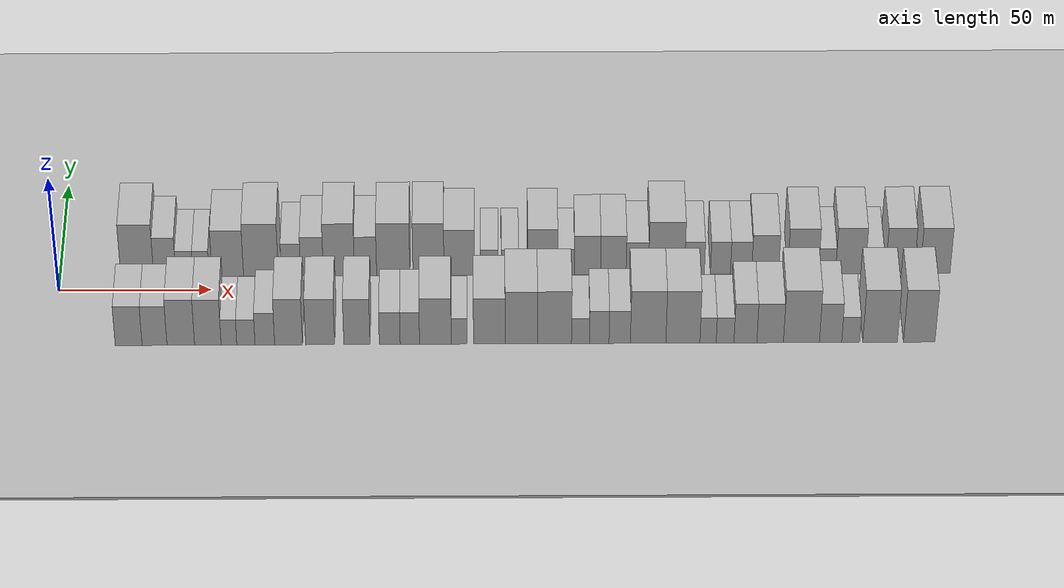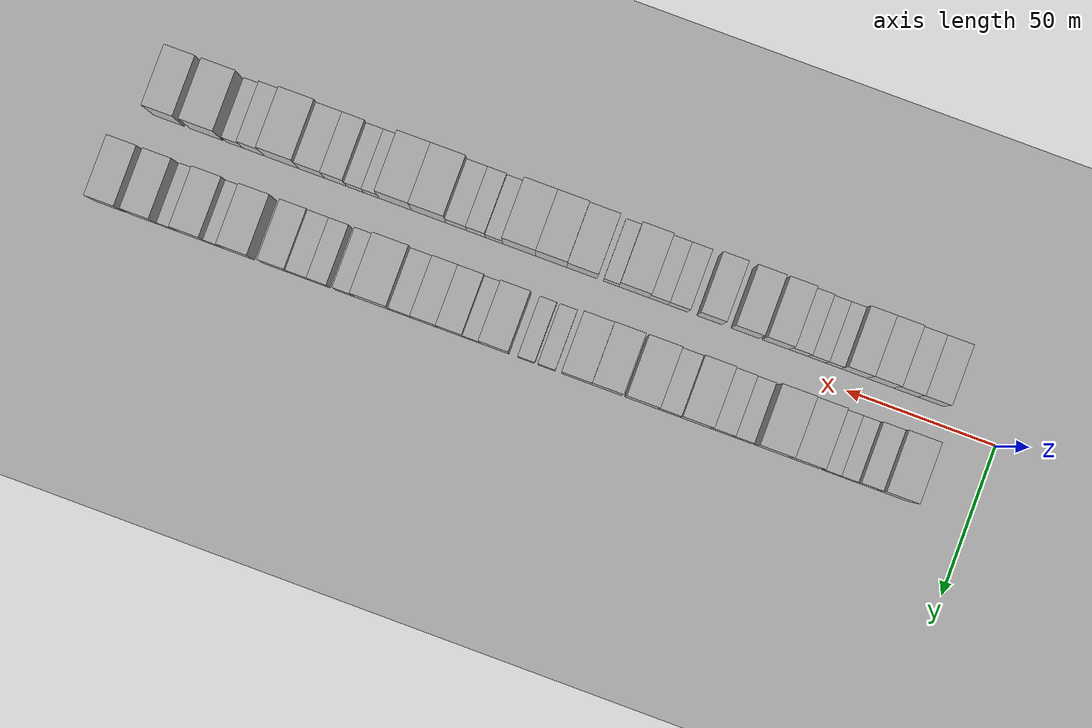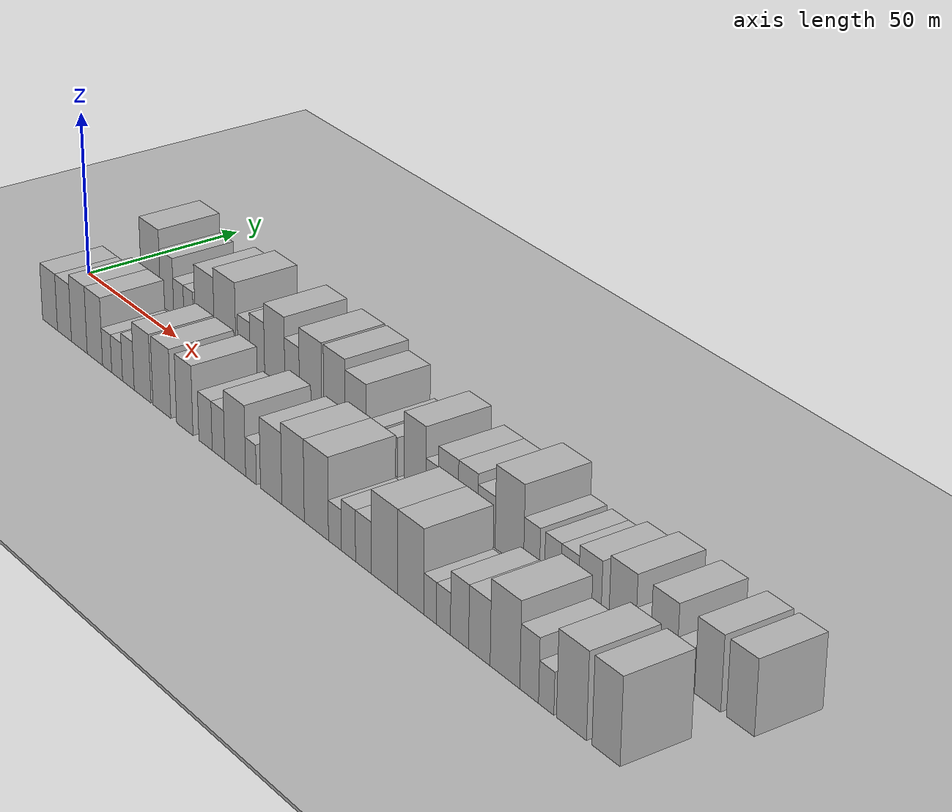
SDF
<?xml version="1.0" encoding="utf-8"?>

<sdf version="1.6">

   <world name="default">

      <gui fullscreen="0">

         <camera name="user_camera">

            <pose>-15 0 4.57585 0 0 0</pose>

            <view_controller>orbit</view_controller>

         </camera>

      </gui>

      <scene>

         <sky>

           <clouds>

             <speed>12</speed>

           </clouds>

         </sky>

         <ambient>0.4 0.4 0.4 1</ambient>

         <background>0.7 0.7 0.7 1</background>

         <shadows>1</shadows>

      </scene>

      <gravity>0 0 -9.8066</gravity>

      <magnetic_field>6e-06 2.3e-05 -4.2e-05</magnetic_field>

      <physics default="0" name="default_physics" type="ode">

         <ode>

            <solver>

               <type>quick</type>

               <iters>10</iters>

               <sor>1.0</sor>

               <use_dynamic_moi_rescaling>0</use_dynamic_moi_rescaling>

            </solver>

            <constraints>

               <cfm>0</cfm>

               <erp>0.2</erp>

               <contact_max_correcting_vel>100</contact_max_correcting_vel>

               <contact_surface_layer>0.001</contact_surface_layer>

            </constraints>

         </ode>

         <max_step_size>0.004</max_step_size>

         <real_time_factor>1</real_time_factor>

         <real_time_update_rate>250</real_time_update_rate>

      </physics>

      <light name="sun" type="directional">

         <cast_shadows>1</cast_shadows>

         <pose>0 0 10 0 0 0</pose>

         <diffuse>0.8 0.8 0.8 1</diffuse>

         <specular>0.2 0.2 0.2 1</specular>

         <attenuation>

            <range>1000</range>

            <constant>0.9</constant>

            <linear>0.01</linear>

            <quadratic>0.001</quadratic>

         </attenuation>

         <direction>-0.5 0.1 -0.9</direction>

      </light>

      <include>

         <name>ground_plane_1</name>

         <uri>model://HANNAS_ground_plane</uri>

         <pose>0 0 0  0 0 0</pose>

      </include>

      <include>

         <name>ground_plane_2</name>

         <uri>model://HANNAS_ground_plane</uri>

         <pose>100 0 0  0 0 0</pose>

      </include>

      <model name="building_1">

         <static>1</static>

         <pose frame="">25.4195 16.0000 0 0.000000 0.000000 1.570796</pose>

         <link name="link">

            <pose frame="">0 0 12.00 0 0 0</pose>

            <collision name="collision">

               <geometry>

                  <box>

                     <size>20.0000 10.8389 24.0000</size>

                  </box>

               </geometry>

               <max_contacts>10</max_contacts>

               <surface>

                  <contact>

                     <ode/>

                  </contact>

                  <bounce/>

                  <friction>

                     <torsional>

                        <ode/>

                     </torsional>

                     <ode/>

                  </friction>

               </surface>

            </collision>

            <visual name="visual">

               <cast_shadows>0</cast_shadows>

               <geometry>

                  <box>

                     <size>20.0000 10.8389 24.0000</size>

                  </box>

               </geometry>

               <material>

                  <script>

                     <uri>model://HANNAS_wall/materials/scripts</uri>

                     <uri>model://HANNAS_wall/materials/textures</uri>

                     <name>vrc/HANNAS_wall</name>

                  </script>

               </material>

            </visual>

            <self_collide>0</self_collide>

            <enable_wind>0</enable_wind>

            <kinematic>0</kinematic>

         </link>

      </model>

      <model name="building_2">

         <static>1</static>

         <pose frame="">34.4876 16.0000 0 0.000000 0.000000 1.570796</pose>

         <link name="link">

            <pose frame="">0 0 9.00 0 0 0</pose>

            <collision name="collision">

               <geometry>

                  <box>

                     <size>20.0000 7.2974 18.0000</size>

                  </box>

               </geometry>

               <max_contacts>10</max_contacts>

               <surface>

                  <contact>

                     <ode/>

                  </contact>

                  <bounce/>

                  <friction>

                     <torsional>

                        <ode/>

                     </torsional>

                     <ode/>

                  </friction>

               </surface>

            </collision>

            <visual name="visual">

               <cast_shadows>0</cast_shadows>

               <geometry>

                  <box>

                     <size>20.0000 7.2974 18.0000</size>

                  </box>

               </geometry>

               <material>

                  <script>

                     <uri>model://HANNAS_wall/materials/scripts</uri>

                     <uri>model://HANNAS_wall/materials/textures</uri>

                     <name>vrc/HANNAS_wall</name>

                  </script>

               </material>

            </visual>

            <self_collide>0</self_collide>

            <enable_wind>0</enable_wind>

            <kinematic>0</kinematic>

         </link>

      </model>

      <model name="building_3">

         <static>1</static>

         <pose frame="">40.9584 16.0000 0 0.000000 0.000000 1.570796</pose>

         <link name="link">

            <pose frame="">0 0 6.00 0 0 0</pose>

            <collision name="collision">

               <geometry>

                  <box>

                     <size>20.0000 5.6441 12.0000</size>

                  </box>

               </geometry>

               <max_contacts>10</max_contacts>

               <surface>

                  <contact>

                     <ode/>

                  </contact>

                  <bounce/>

                  <friction>

                     <torsional>

                        <ode/>

                     </torsional>

                     <ode/>

                  </friction>

               </surface>

            </collision>

            <visual name="visual">

               <cast_shadows>0</cast_shadows>

               <geometry>

                  <box>

                     <size>20.0000 5.6441 12.0000</size>

                  </box>

               </geometry>

               <material>

                  <script>

                     <uri>model://HANNAS_wall/materials/scripts</uri>

                     <uri>model://HANNAS_wall/materials/textures</uri>

                     <name>vrc/HANNAS_wall</name>

                  </script>

               </material>

            </visual>

            <self_collide>0</self_collide>

            <enable_wind>0</enable_wind>

            <kinematic>0</kinematic>

         </link>

      </model>

      <model name="building_4">

         <static>1</static>

         <pose frame="">46.4162 16.0000 0 0.000000 0.000000 1.570796</pose>

         <link name="link">

            <pose frame="">0 0 6.00 0 0 0</pose>

            <collision name="collision">

               <geometry>

                  <box>

                     <size>20.0000 5.2715 12.0000</size>

                  </box>

               </geometry>

               <max_contacts>10</max_contacts>

               <surface>

                  <contact>

                     <ode/>

                  </contact>

                  <bounce/>

                  <friction>

                     <torsional>

                        <ode/>

                     </torsional>

                     <ode/>

                  </friction>

               </surface>

            </collision>

            <visual name="visual">

               <cast_shadows>0</cast_shadows>

               <geometry>

                  <box>

                     <size>20.0000 5.2715 12.0000</size>

                  </box>

               </geometry>

               <material>

                  <script>

                     <uri>model://HANNAS_wall/materials/scripts</uri>

                     <uri>model://HANNAS_wall/materials/textures</uri>

                     <name>vrc/HANNAS_wall</name>

                  </script>

               </material>

            </visual>

            <self_collide>0</self_collide>

            <enable_wind>0</enable_wind>

            <kinematic>0</kinematic>

         </link>

      </model>

      <model name="building_5">

         <static>1</static>

         <pose frame="">55.2350 16.0000 0 0.000000 0.000000 1.570796</pose>

         <link name="link">

            <pose frame="">0 0 10.50 0 0 0</pose>

            <collision name="collision">

               <geometry>

                  <box>

                     <size>20.0000 10.3663 21.0000</size>

                  </box>

               </geometry>

               <max_contacts>10</max_contacts>

               <surface>

                  <contact>

                     <ode/>

                  </contact>

                  <bounce/>

                  <friction>

                     <torsional>

                        <ode/>

                     </torsional>

                     <ode/>

                  </friction>

               </surface>

            </collision>

            <visual name="visual">

               <cast_shadows>0</cast_shadows>

               <geometry>

                  <box>

                     <size>20.0000 10.3663 21.0000</size>

                  </box>

               </geometry>

               <material>

                  <script>

                     <uri>model://HANNAS_wall/materials/scripts</uri>

                     <uri>model://HANNAS_wall/materials/textures</uri>

                     <name>vrc/HANNAS_wall</name>

                  </script>

               </material>

            </visual>

            <self_collide>0</self_collide>

            <enable_wind>0</enable_wind>

            <kinematic>0</kinematic>

         </link>

      </model>

      <model name="building_6">

         <static>1</static>

         <pose frame="">66.1503 16.0000 0 0.000000 0.000000 1.570796</pose>

         <link name="link">

            <pose frame="">0 0 12.00 0 0 0</pose>

            <collision name="collision">

               <geometry>

                  <box>

                     <size>20.0000 11.4643 24.0000</size>

                  </box>

               </geometry>

               <max_contacts>10</max_contacts>

               <surface>

                  <contact>

                     <ode/>

                  </contact>

                  <bounce/>

                  <friction>

                     <torsional>

                        <ode/>

                     </torsional>

                     <ode/>

                  </friction>

               </surface>

            </collision>

            <visual name="visual">

               <cast_shadows>0</cast_shadows>

               <geometry>

                  <box>

                     <size>20.0000 11.4643 24.0000</size>

                  </box>

               </geometry>

               <material>

                  <script>

                     <uri>model://HANNAS_wall/materials/scripts</uri>

                     <uri>model://HANNAS_wall/materials/textures</uri>

                     <name>vrc/HANNAS_wall</name>

                  </script>

               </material>

            </visual>

            <self_collide>0</self_collide>

            <enable_wind>0</enable_wind>

            <kinematic>0</kinematic>

         </link>

      </model>

      <model name="building_7">

         <static>1</static>

         <pose frame="">76.0640 16.0000 0 0.000000 0.000000 1.570796</pose>

         <link name="link">

            <pose frame="">0 0 7.50 0 0 0</pose>

            <collision name="collision">

               <geometry>

                  <box>

                     <size>20.0000 6.3631 15.0000</size>

                  </box>

               </geometry>

               <max_contacts>10</max_contacts>

               <surface>

                  <contact>

                     <ode/>

                  </contact>

                  <bounce/>

                  <friction>

                     <torsional>

                        <ode/>

                     </torsional>

                     <ode/>

                  </friction>

               </surface>

            </collision>

            <visual name="visual">

               <cast_shadows>0</cast_shadows>

               <geometry>

                  <box>

                     <size>20.0000 6.3631 15.0000</size>

                  </box>

               </geometry>

               <material>

                  <script>

                     <uri>model://HANNAS_wall/materials/scripts</uri>

                     <uri>model://HANNAS_wall/materials/textures</uri>

                     <name>vrc/HANNAS_wall</name>

                  </script>

               </material>

            </visual>

            <self_collide>0</self_collide>

            <enable_wind>0</enable_wind>

            <kinematic>0</kinematic>

         </link>

      </model>

      <model name="building_8">

         <static>1</static>

         <pose frame="">82.9743 16.0000 0 0.000000 0.000000 1.570796</pose>

         <link name="link">

            <pose frame="">0 0 9.00 0 0 0</pose>

            <collision name="collision">

               <geometry>

                  <box>

                     <size>20.0000 7.4576 18.0000</size>

                  </box>

               </geometry>

               <max_contacts>10</max_contacts>

               <surface>

                  <contact>

                     <ode/>

                  </contact>

                  <bounce/>

                  <friction>

                     <torsional>

                        <ode/>

                     </torsional>

                     <ode/>

                  </friction>

               </surface>

            </collision>

            <visual name="visual">

               <cast_shadows>0</cast_shadows>

               <geometry>

                  <box>

                     <size>20.0000 7.4576 18.0000</size>

                  </box>

               </geometry>

               <material>

                  <script>

                     <uri>model://HANNAS_wall/materials/scripts</uri>

                     <uri>model://HANNAS_wall/materials/textures</uri>

                     <name>vrc/HANNAS_wall</name>

                  </script>

               </material>

            </visual>

            <self_collide>0</self_collide>

            <enable_wind>0</enable_wind>

            <kinematic>0</kinematic>

         </link>

      </model>

      <model name="building_9">

         <static>1</static>

         <pose frame="">91.8453 16.0000 0 0.000000 0.000000 1.570796</pose>

         <link name="link">

            <pose frame="">0 0 12.00 0 0 0</pose>

            <collision name="collision">

               <geometry>

                  <box>

                     <size>20.0000 10.2842 24.0000</size>

                  </box>

               </geometry>

               <max_contacts>10</max_contacts>

               <surface>

                  <contact>

                     <ode/>

                  </contact>

                  <bounce/>

                  <friction>

                     <torsional>

                        <ode/>

                     </torsional>

                     <ode/>

                  </friction>

               </surface>

            </collision>

            <visual name="visual">

               <cast_shadows>0</cast_shadows>

               <geometry>

                  <box>

                     <size>20.0000 10.2842 24.0000</size>

                  </box>

               </geometry>

               <material>

                  <script>

                     <uri>model://HANNAS_wall/materials/scripts</uri>

                     <uri>model://HANNAS_wall/materials/textures</uri>

                     <name>vrc/HANNAS_wall</name>

                  </script>

               </material>

            </visual>

            <self_collide>0</self_collide>

            <enable_wind>0</enable_wind>

            <kinematic>0</kinematic>

         </link>

      </model>

      <model name="building_10">

         <static>1</static>

         <pose frame="">100.6256 16.0000 0 0.000000 0.000000 1.570796</pose>

         <link name="link">

            <pose frame="">0 0 9.00 0 0 0</pose>

            <collision name="collision">

               <geometry>

                  <box>

                     <size>20.0000 7.2764 18.0000</size>

                  </box>

               </geometry>

               <max_contacts>10</max_contacts>

               <surface>

                  <contact>

                     <ode/>

                  </contact>

                  <bounce/>

                  <friction>

                     <torsional>

                        <ode/>

                     </torsional>

                     <ode/>

                  </friction>

               </surface>

            </collision>

            <visual name="visual">

               <cast_shadows>0</cast_shadows>

               <geometry>

                  <box>

                     <size>20.0000 7.2764 18.0000</size>

                  </box>

               </geometry>

               <material>

                  <script>

                     <uri>model://HANNAS_wall/materials/scripts</uri>

                     <uri>model://HANNAS_wall/materials/textures</uri>

                     <name>vrc/HANNAS_wall</name>

                  </script>

               </material>

            </visual>

            <self_collide>0</self_collide>

            <enable_wind>0</enable_wind>

            <kinematic>0</kinematic>

         </link>

      </model>

      <model name="building_11">

         <static>1</static>

         <pose frame="">109.7319 16.0000 0 0.000000 0.000000 1.570796</pose>

         <link name="link">

            <pose frame="">0 0 12.00 0 0 0</pose>

            <collision name="collision">

               <geometry>

                  <box>

                     <size>20.0000 10.9363 24.0000</size>

                  </box>

               </geometry>

               <max_contacts>10</max_contacts>

               <surface>

                  <contact>

                     <ode/>

                  </contact>

                  <bounce/>

                  <friction>

                     <torsional>

                        <ode/>

                     </torsional>

                     <ode/>

                  </friction>

               </surface>

            </collision>

            <visual name="visual">

               <cast_shadows>0</cast_shadows>

               <geometry>

                  <box>

                     <size>20.0000 10.9363 24.0000</size>

                  </box>

               </geometry>

               <material>

                  <script>

                     <uri>model://HANNAS_wall/materials/scripts</uri>

                     <uri>model://HANNAS_wall/materials/textures</uri>

                     <name>vrc/HANNAS_wall</name>

                  </script>

               </material>

            </visual>

            <self_collide>0</self_collide>

            <enable_wind>0</enable_wind>

            <kinematic>0</kinematic>

         </link>

      </model>

      <model name="building_12">

         <static>1</static>

         <pose frame="">121.3210 16.0000 0 0.000000 0.000000 1.570796</pose>

         <link name="link">

            <pose frame="">0 0 12.00 0 0 0</pose>

            <collision name="collision">

               <geometry>

                  <box>

                     <size>20.0000 10.2417 24.0000</size>

                  </box>

               </geometry>

               <max_contacts>10</max_contacts>

               <surface>

                  <contact>

                     <ode/>

                  </contact>

                  <bounce/>

                  <friction>

                     <torsional>

                        <ode/>

                     </torsional>

                     <ode/>

                  </friction>

               </surface>

            </collision>

            <visual name="visual">

               <cast_shadows>0</cast_shadows>

               <geometry>

                  <box>

                     <size>20.0000 10.2417 24.0000</size>

                  </box>

               </geometry>

               <material>

                  <script>

                     <uri>model://HANNAS_wall/materials/scripts</uri>

                     <uri>model://HANNAS_wall/materials/textures</uri>

                     <name>vrc/HANNAS_wall</name>

                  </script>

               </material>

            </visual>

            <self_collide>0</self_collide>

            <enable_wind>0</enable_wind>

            <kinematic>0</kinematic>

         </link>

      </model>

      <model name="building_13">

         <static>1</static>

         <pose frame="">131.4453 16.0000 0 0.000000 0.000000 1.570796</pose>

         <link name="link">

            <pose frame="">0 0 10.50 0 0 0</pose>

            <collision name="collision">

               <geometry>

                  <box>

                     <size>20.0000 10.0069 21.0000</size>

                  </box>

               </geometry>

               <max_contacts>10</max_contacts>

               <surface>

                  <contact>

                     <ode/>

                  </contact>

                  <bounce/>

                  <friction>

                     <torsional>

                        <ode/>

                     </torsional>

                     <ode/>

                  </friction>

               </surface>

            </collision>

            <visual name="visual">

               <cast_shadows>0</cast_shadows>

               <geometry>

                  <box>

                     <size>20.0000 10.0069 21.0000</size>

                  </box>

               </geometry>

               <material>

                  <script>

                     <uri>model://HANNAS_wall/materials/scripts</uri>

                     <uri>model://HANNAS_wall/materials/textures</uri>

                     <name>vrc/HANNAS_wall</name>

                  </script>

               </material>

            </visual>

            <self_collide>0</self_collide>

            <enable_wind>0</enable_wind>

            <kinematic>0</kinematic>

         </link>

      </model>

      <model name="building_14">

         <static>1</static>

         <pose frame="">141.3800 16.0000 0 0.000000 0.000000 1.570796</pose>

         <link name="link">

            <pose frame="">0 0 6.00 0 0 0</pose>

            <collision name="collision">

               <geometry>

                  <box>

                     <size>20.0000 5.8627 12.0000</size>

                  </box>

               </geometry>

               <max_contacts>10</max_contacts>

               <surface>

                  <contact>

                     <ode/>

                  </contact>

                  <bounce/>

                  <friction>

                     <torsional>

                        <ode/>

                     </torsional>

                     <ode/>

                  </friction>

               </surface>

            </collision>

            <visual name="visual">

               <cast_shadows>0</cast_shadows>

               <geometry>

                  <box>

                     <size>20.0000 5.8627 12.0000</size>

                  </box>

               </geometry>

               <material>

                  <script>

                     <uri>model://HANNAS_wall/materials/scripts</uri>

                     <uri>model://HANNAS_wall/materials/textures</uri>

                     <name>vrc/HANNAS_wall</name>

                  </script>

               </material>

            </visual>

            <self_collide>0</self_collide>

            <enable_wind>0</enable_wind>

            <kinematic>0</kinematic>

         </link>

      </model>

      <model name="building_15">

         <static>1</static>

         <pose frame="">148.1402 16.0000 0 0.000000 0.000000 1.570796</pose>

         <link name="link">

            <pose frame="">0 0 6.00 0 0 0</pose>

            <collision name="collision">

               <geometry>

                  <box>

                     <size>20.0000 5.6575 12.0000</size>

                  </box>

               </geometry>

               <max_contacts>10</max_contacts>

               <surface>

                  <contact>

                     <ode/>

                  </contact>

                  <bounce/>

                  <friction>

                     <torsional>

                        <ode/>

                     </torsional>

                     <ode/>

                  </friction>

               </surface>

            </collision>

            <visual name="visual">

               <cast_shadows>0</cast_shadows>

               <geometry>

                  <box>

                     <size>20.0000 5.6575 12.0000</size>

                  </box>

               </geometry>

               <material>

                  <script>

                     <uri>model://HANNAS_wall/materials/scripts</uri>

                     <uri>model://HANNAS_wall/materials/textures</uri>

                     <name>vrc/HANNAS_wall</name>

                  </script>

               </material>

            </visual>

            <self_collide>0</self_collide>

            <enable_wind>0</enable_wind>

            <kinematic>0</kinematic>

         </link>

      </model>

      <model name="building_16">

         <static>1</static>

         <pose frame="">158.8875 16.0000 0 0.000000 0.000000 1.570796</pose>

         <link name="link">

            <pose frame="">0 0 10.50 0 0 0</pose>

            <collision name="collision">

               <geometry>

                  <box>

                     <size>20.0000 9.8371 21.0000</size>

                  </box>

               </geometry>

               <max_contacts>10</max_contacts>

               <surface>

                  <contact>

                     <ode/>

                  </contact>

                  <bounce/>

                  <friction>

                     <torsional>

                        <ode/>

                     </torsional>

                     <ode/>

                  </friction>

               </surface>

            </collision>

            <visual name="visual">

               <cast_shadows>0</cast_shadows>

               <geometry>

                  <box>

                     <size>20.0000 9.8371 21.0000</size>

                  </box>

               </geometry>

               <material>

                  <script>

                     <uri>model://HANNAS_wall/materials/scripts</uri>

                     <uri>model://HANNAS_wall/materials/textures</uri>

                     <name>vrc/HANNAS_wall</name>

                  </script>

               </material>

            </visual>

            <self_collide>0</self_collide>

            <enable_wind>0</enable_wind>

            <kinematic>0</kinematic>

         </link>

      </model>

      <model name="building_17">

         <static>1</static>

         <pose frame="">166.5775 16.0000 0 0.000000 0.000000 1.570796</pose>

         <link name="link">

            <pose frame="">0 0 6.00 0 0 0</pose>

            <collision name="collision">

               <geometry>

                  <box>

                     <size>20.0000 5.5429 12.0000</size>

                  </box>

               </geometry>

               <max_contacts>10</max_contacts>

               <surface>

                  <contact>

                     <ode/>

                  </contact>

                  <bounce/>

                  <friction>

                     <torsional>

                        <ode/>

                     </torsional>

                     <ode/>

                  </friction>

               </surface>

            </collision>

            <visual name="visual">

               <cast_shadows>0</cast_shadows>

               <geometry>

                  <box>

                     <size>20.0000 5.5429 12.0000</size>

                  </box>

               </geometry>

               <material>

                  <script>

                     <uri>model://HANNAS_wall/materials/scripts</uri>

                     <uri>model://HANNAS_wall/materials/textures</uri>

                     <name>vrc/HANNAS_wall</name>

                  </script>

               </material>

            </visual>

            <self_collide>0</self_collide>

            <enable_wind>0</enable_wind>

            <kinematic>0</kinematic>

         </link>

      </model>

      <model name="building_18">

         <static>1</static>

         <pose frame="">173.6655 16.0000 0 0.000000 0.000000 1.570796</pose>

         <link name="link">

            <pose frame="">0 0 9.00 0 0 0</pose>

            <collision name="collision">

               <geometry>

                  <box>

                     <size>20.0000 8.6331 18.0000</size>

                  </box>

               </geometry>

               <max_contacts>10</max_contacts>

               <surface>

                  <contact>

                     <ode/>

                  </contact>

                  <bounce/>

                  <friction>

                     <torsional>

                        <ode/>

                     </torsional>

                     <ode/>

                  </friction>

               </surface>

            </collision>

            <visual name="visual">

               <cast_shadows>0</cast_shadows>

               <geometry>

                  <box>

                     <size>20.0000 8.6331 18.0000</size>

                  </box>

               </geometry>

               <material>

                  <script>

                     <uri>model://HANNAS_wall/materials/scripts</uri>

                     <uri>model://HANNAS_wall/materials/textures</uri>

                     <name>vrc/HANNAS_wall</name>

                  </script>

               </material>

            </visual>

            <self_collide>0</self_collide>

            <enable_wind>0</enable_wind>

            <kinematic>0</kinematic>

         </link>

      </model>

      <model name="building_19">

         <static>1</static>

         <pose frame="">182.2064 16.0000 0 0.000000 0.000000 1.570796</pose>

         <link name="link">

            <pose frame="">0 0 9.00 0 0 0</pose>

            <collision name="collision">

               <geometry>

                  <box>

                     <size>20.0000 8.4489 18.0000</size>

                  </box>

               </geometry>

               <max_contacts>10</max_contacts>

               <surface>

                  <contact>

                     <ode/>

                  </contact>

                  <bounce/>

                  <friction>

                     <torsional>

                        <ode/>

                     </torsional>

                     <ode/>

                  </friction>

               </surface>

            </collision>

            <visual name="visual">

               <cast_shadows>0</cast_shadows>

               <geometry>

                  <box>

                     <size>20.0000 8.4489 18.0000</size>

                  </box>

               </geometry>

               <material>

                  <script>

                     <uri>model://HANNAS_wall/materials/scripts</uri>

                     <uri>model://HANNAS_wall/materials/textures</uri>

                     <name>vrc/HANNAS_wall</name>

                  </script>

               </material>

            </visual>

            <self_collide>0</self_collide>

            <enable_wind>0</enable_wind>

            <kinematic>0</kinematic>

         </link>

      </model>

      <model name="building_20">

         <static>1</static>

         <pose frame="">190.1154 16.0000 0 0.000000 0.000000 1.570796</pose>

         <link name="link">

            <pose frame="">0 0 7.50 0 0 0</pose>

            <collision name="collision">

               <geometry>

                  <box>

                     <size>20.0000 7.3691 15.0000</size>

                  </box>

               </geometry>

               <max_contacts>10</max_contacts>

               <surface>

                  <contact>

                     <ode/>

                  </contact>

                  <bounce/>

                  <friction>

                     <torsional>

                        <ode/>

                     </torsional>

                     <ode/>

                  </friction>

               </surface>

            </collision>

            <visual name="visual">

               <cast_shadows>0</cast_shadows>

               <geometry>

                  <box>

                     <size>20.0000 7.3691 15.0000</size>

                  </box>

               </geometry>

               <material>

                  <script>

                     <uri>model://HANNAS_wall/materials/scripts</uri>

                     <uri>model://HANNAS_wall/materials/textures</uri>

                     <name>vrc/HANNAS_wall</name>

                  </script>

               </material>

            </visual>

            <self_collide>0</self_collide>

            <enable_wind>0</enable_wind>

            <kinematic>0</kinematic>

         </link>

      </model>

      <model name="building_21">

         <static>1</static>

         <pose frame="">199.7422 16.0000 0 0.000000 0.000000 1.570796</pose>

         <link name="link">

            <pose frame="">0 0 12.00 0 0 0</pose>

            <collision name="collision">

               <geometry>

                  <box>

                     <size>20.0000 11.8844 24.0000</size>

                  </box>

               </geometry>

               <max_contacts>10</max_contacts>

               <surface>

                  <contact>

                     <ode/>

                  </contact>

                  <bounce/>

                  <friction>

                     <torsional>

                        <ode/>

                     </torsional>

                     <ode/>

                  </friction>

               </surface>

            </collision>

            <visual name="visual">

               <cast_shadows>0</cast_shadows>

               <geometry>

                  <box>

                     <size>20.0000 11.8844 24.0000</size>

                  </box>

               </geometry>

               <material>

                  <script>

                     <uri>model://HANNAS_wall/materials/scripts</uri>

                     <uri>model://HANNAS_wall/materials/textures</uri>

                     <name>vrc/HANNAS_wall</name>

                  </script>

               </material>

            </visual>

            <self_collide>0</self_collide>

            <enable_wind>0</enable_wind>

            <kinematic>0</kinematic>

         </link>

      </model>

      <model name="building_22">

         <static>1</static>

         <pose frame="">208.9534 16.0000 0 0.000000 0.000000 1.570796</pose>

         <link name="link">

            <pose frame="">0 0 7.50 0 0 0</pose>

            <collision name="collision">

               <geometry>

                  <box>

                     <size>20.0000 6.5379 15.0000</size>

                  </box>

               </geometry>

               <max_contacts>10</max_contacts>

               <surface>

                  <contact>

                     <ode/>

                  </contact>

                  <bounce/>

                  <friction>

                     <torsional>

                        <ode/>

                     </torsional>

                     <ode/>

                  </friction>

               </surface>

            </collision>

            <visual name="visual">

               <cast_shadows>0</cast_shadows>

               <geometry>

                  <box>

                     <size>20.0000 6.5379 15.0000</size>

                  </box>

               </geometry>

               <material>

                  <script>

                     <uri>model://HANNAS_wall/materials/scripts</uri>

                     <uri>model://HANNAS_wall/materials/textures</uri>

                     <name>vrc/HANNAS_wall</name>

                  </script>

               </material>

            </visual>

            <self_collide>0</self_collide>

            <enable_wind>0</enable_wind>

            <kinematic>0</kinematic>

         </link>

      </model>

      <model name="building_23">

         <static>1</static>

         <pose frame="">217.5202 16.0000 0 0.000000 0.000000 1.570796</pose>

         <link name="link">

            <pose frame="">0 0 7.50 0 0 0</pose>

            <collision name="collision">

               <geometry>

                  <box>

                     <size>20.0000 6.5957 15.0000</size>

                  </box>

               </geometry>

               <max_contacts>10</max_contacts>

               <surface>

                  <contact>

                     <ode/>

                  </contact>

                  <bounce/>

                  <friction>

                     <torsional>

                        <ode/>

                     </torsional>

                     <ode/>

                  </friction>

               </surface>

            </collision>

            <visual name="visual">

               <cast_shadows>0</cast_shadows>

               <geometry>

                  <box>

                     <size>20.0000 6.5957 15.0000</size>

                  </box>

               </geometry>

               <material>

                  <script>

                     <uri>model://HANNAS_wall/materials/scripts</uri>

                     <uri>model://HANNAS_wall/materials/textures</uri>

                     <name>vrc/HANNAS_wall</name>

                  </script>

               </material>

            </visual>

            <self_collide>0</self_collide>

            <enable_wind>0</enable_wind>

            <kinematic>0</kinematic>

         </link>

      </model>

      <model name="building_24">

         <static>1</static>

         <pose frame="">224.3153 16.0000 0 0.000000 0.000000 1.570796</pose>

         <link name="link">

            <pose frame="">0 0 7.50 0 0 0</pose>

            <collision name="collision">

               <geometry>

                  <box>

                     <size>20.0000 6.9945 15.0000</size>

                  </box>

               </geometry>

               <max_contacts>10</max_contacts>

               <surface>

                  <contact>

                     <ode/>

                  </contact>

                  <bounce/>

                  <friction>

                     <torsional>

                        <ode/>

                     </torsional>

                     <ode/>

                  </friction>

               </surface>

            </collision>

            <visual name="visual">

               <cast_shadows>0</cast_shadows>

               <geometry>

                  <box>

                     <size>20.0000 6.9945 15.0000</size>

                  </box>

               </geometry>

               <material>

                  <script>

                     <uri>model://HANNAS_wall/materials/scripts</uri>

                     <uri>model://HANNAS_wall/materials/textures</uri>

                     <name>vrc/HANNAS_wall</name>

                  </script>

               </material>

            </visual>

            <self_collide>0</self_collide>

            <enable_wind>0</enable_wind>

            <kinematic>0</kinematic>

         </link>

      </model>

      <model name="building_25">

         <static>1</static>

         <pose frame="">232.2512 16.0000 0 0.000000 0.000000 1.570796</pose>

         <link name="link">

            <pose frame="">0 0 9.00 0 0 0</pose>

            <collision name="collision">

               <geometry>

                  <box>

                     <size>20.0000 8.8774 18.0000</size>

                  </box>

               </geometry>

               <max_contacts>10</max_contacts>

               <surface>

                  <contact>

                     <ode/>

                  </contact>

                  <bounce/>

                  <friction>

                     <torsional>

                        <ode/>

                     </torsional>

                     <ode/>

                  </friction>

               </surface>

            </collision>

            <visual name="visual">

               <cast_shadows>0</cast_shadows>

               <geometry>

                  <box>

                     <size>20.0000 8.8774 18.0000</size>

                  </box>

               </geometry>

               <material>

                  <script>

                     <uri>model://HANNAS_wall/materials/scripts</uri>

                     <uri>model://HANNAS_wall/materials/textures</uri>

                     <name>vrc/HANNAS_wall</name>

                  </script>

               </material>

            </visual>

            <self_collide>0</self_collide>

            <enable_wind>0</enable_wind>

            <kinematic>0</kinematic>

         </link>

      </model>

      <model name="building_26">

         <static>1</static>

         <pose frame="">244.7805 16.0000 0 0.000000 0.000000 1.570796</pose>

         <link name="link">

            <pose frame="">0 0 10.50 0 0 0</pose>

            <collision name="collision">

               <geometry>

                  <box>

                     <size>20.0000 10.1812 21.0000</size>

                  </box>

               </geometry>

               <max_contacts>10</max_contacts>

               <surface>

                  <contact>

                     <ode/>

                  </contact>

                  <bounce/>

                  <friction>

                     <torsional>

                        <ode/>

                     </torsional>

                     <ode/>

                  </friction>

               </surface>

            </collision>

            <visual name="visual">

               <cast_shadows>0</cast_shadows>

               <geometry>

                  <box>

                     <size>20.0000 10.1812 21.0000</size>

                  </box>

               </geometry>

               <material>

                  <script>

                     <uri>model://HANNAS_wall/materials/scripts</uri>

                     <uri>model://HANNAS_wall/materials/textures</uri>

                     <name>vrc/HANNAS_wall</name>

                  </script>

               </material>

            </visual>

            <self_collide>0</self_collide>

            <enable_wind>0</enable_wind>

            <kinematic>0</kinematic>

         </link>

      </model>

      <model name="building_27">

         <static>1</static>

         <pose frame="">252.6764 16.0000 0 0.000000 0.000000 1.570796</pose>

         <link name="link">

            <pose frame="">0 0 6.00 0 0 0</pose>

            <collision name="collision">

               <geometry>

                  <box>

                     <size>20.0000 5.6105 12.0000</size>

                  </box>

               </geometry>

               <max_contacts>10</max_contacts>

               <surface>

                  <contact>

                     <ode/>

                  </contact>

                  <bounce/>

                  <friction>

                     <torsional>

                        <ode/>

                     </torsional>

                     <ode/>

                  </friction>

               </surface>

            </collision>

            <visual name="visual">

               <cast_shadows>0</cast_shadows>

               <geometry>

                  <box>

                     <size>20.0000 5.6105 12.0000</size>

                  </box>

               </geometry>

               <material>

                  <script>

                     <uri>model://HANNAS_wall/materials/scripts</uri>

                     <uri>model://HANNAS_wall/materials/textures</uri>

                     <name>vrc/HANNAS_wall</name>

                  </script>

               </material>

            </visual>

            <self_collide>0</self_collide>

            <enable_wind>0</enable_wind>

            <kinematic>0</kinematic>

         </link>

      </model>

      <model name="building_28">

         <static>1</static>

         <pose frame="">260.3763 16.0000 0 0.000000 0.000000 1.570796</pose>

         <link name="link">

            <pose frame="">0 0 10.50 0 0 0</pose>

            <collision name="collision">

               <geometry>

                  <box>

                     <size>20.0000 9.7892 21.0000</size>

                  </box>

               </geometry>

               <max_contacts>10</max_contacts>

               <surface>

                  <contact>

                     <ode/>

                  </contact>

                  <bounce/>

                  <friction>

                     <torsional>

                        <ode/>

                     </torsional>

                     <ode/>

                  </friction>

               </surface>

            </collision>

            <visual name="visual">

               <cast_shadows>0</cast_shadows>

               <geometry>

                  <box>

                     <size>20.0000 9.7892 21.0000</size>

                  </box>

               </geometry>

               <material>

                  <script>

                     <uri>model://HANNAS_wall/materials/scripts</uri>

                     <uri>model://HANNAS_wall/materials/textures</uri>

                     <name>vrc/HANNAS_wall</name>

                  </script>

               </material>

            </visual>

            <self_collide>0</self_collide>

            <enable_wind>0</enable_wind>

            <kinematic>0</kinematic>

         </link>

      </model>

      <model name="building_29">

         <static>1</static>

         <pose frame="">268.1109 16.0000 0 0.000000 0.000000 1.570796</pose>

         <link name="link">

            <pose frame="">0 0 6.00 0 0 0</pose>

            <collision name="collision">

               <geometry>

                  <box>

                     <size>20.0000 5.6800 12.0000</size>

                  </box>

               </geometry>

               <max_contacts>10</max_contacts>

               <surface>

                  <contact>

                     <ode/>

                  </contact>

                  <bounce/>

                  <friction>

                     <torsional>

                        <ode/>

                     </torsional>

                     <ode/>

                  </friction>

               </surface>

            </collision>

            <visual name="visual">

               <cast_shadows>0</cast_shadows>

               <geometry>

                  <box>

                     <size>20.0000 5.6800 12.0000</size>

                  </box>

               </geometry>

               <material>

                  <script>

                     <uri>model://HANNAS_wall/materials/scripts</uri>

                     <uri>model://HANNAS_wall/materials/textures</uri>

                     <name>vrc/HANNAS_wall</name>

                  </script>

               </material>

            </visual>

            <self_collide>0</self_collide>

            <enable_wind>0</enable_wind>

            <kinematic>0</kinematic>

         </link>

      </model>

      <model name="building_30">

         <static>1</static>

         <pose frame="">276.6648 16.0000 0 0.000000 0.000000 1.570796</pose>

         <link name="link">

            <pose frame="">0 0 10.50 0 0 0</pose>

            <collision name="collision">

               <geometry>

                  <box>

                     <size>20.0000 9.4278 21.0000</size>

                  </box>

               </geometry>

               <max_contacts>10</max_contacts>

               <surface>

                  <contact>

                     <ode/>

                  </contact>

                  <bounce/>

                  <friction>

                     <torsional>

                        <ode/>

                     </torsional>

                     <ode/>

                  </friction>

               </surface>

            </collision>

            <visual name="visual">

               <cast_shadows>0</cast_shadows>

               <geometry>

                  <box>

                     <size>20.0000 9.4278 21.0000</size>

                  </box>

               </geometry>

               <material>

                  <script>

                     <uri>model://HANNAS_wall/materials/scripts</uri>

                     <uri>model://HANNAS_wall/materials/textures</uri>

                     <name>vrc/HANNAS_wall</name>

                  </script>

               </material>

            </visual>

            <self_collide>0</self_collide>

            <enable_wind>0</enable_wind>

            <kinematic>0</kinematic>

         </link>

      </model>

      <model name="building_31">

         <static>1</static>

         <pose frame="">288.3045 16.0000 0 0.000000 0.000000 1.570796</pose>

         <link name="link">

            <pose frame="">0 0 10.50 0 0 0</pose>

            <collision name="collision">

               <geometry>

                  <box>

                     <size>20.0000 9.8517 21.0000</size>

                  </box>

               </geometry>

               <max_contacts>10</max_contacts>

               <surface>

                  <contact>

                     <ode/>

                  </contact>

                  <bounce/>

                  <friction>

                     <torsional>

                        <ode/>

                     </torsional>

                     <ode/>

                  </friction>

               </surface>

            </collision>

            <visual name="visual">

               <cast_shadows>0</cast_shadows>

               <geometry>

                  <box>

                     <size>20.0000 9.8517 21.0000</size>

                  </box>

               </geometry>

               <material>

                  <script>

                     <uri>model://HANNAS_wall/materials/scripts</uri>

                     <uri>model://HANNAS_wall/materials/textures</uri>

                     <name>vrc/HANNAS_wall</name>

                  </script>

               </material>

            </visual>

            <self_collide>0</self_collide>

            <enable_wind>0</enable_wind>

            <kinematic>0</kinematic>

         </link>

      </model>

      <model name="building_32">

         <static>1</static>

         <pose frame="">24.3452 -16.0000 0 0.000000 0.000000 1.570796</pose>

         <link name="link">

            <pose frame="">0 0 9.00 0 0 0</pose>

            <collision name="collision">

               <geometry>

                  <box>

                     <size>20.0000 8.6905 18.0000</size>

                  </box>

               </geometry>

               <max_contacts>10</max_contacts>

               <surface>

                  <contact>

                     <ode/>

                  </contact>

                  <bounce/>

                  <friction>

                     <torsional>

                        <ode/>

                     </torsional>

                     <ode/>

                  </friction>

               </surface>

            </collision>

            <visual name="visual">

               <cast_shadows>0</cast_shadows>

               <geometry>

                  <box>

                     <size>20.0000 8.6905 18.0000</size>

                  </box>

               </geometry>

               <material>

                  <script>

                     <uri>model://HANNAS_wall/materials/scripts</uri>

                     <uri>model://HANNAS_wall/materials/textures</uri>

                     <name>vrc/HANNAS_wall</name>

                  </script>

               </material>

            </visual>

            <self_collide>0</self_collide>

            <enable_wind>0</enable_wind>

            <kinematic>0</kinematic>

         </link>

      </model>

      <model name="building_33">

         <static>1</static>

         <pose frame="">32.7283 -16.0000 0 0.000000 0.000000 1.570796</pose>

         <link name="link">

            <pose frame="">0 0 9.00 0 0 0</pose>

            <collision name="collision">

               <geometry>

                  <box>

                     <size>20.0000 8.0757 18.0000</size>

                  </box>

               </geometry>

               <max_contacts>10</max_contacts>

               <surface>

                  <contact>

                     <ode/>

                  </contact>

                  <bounce/>

                  <friction>

                     <torsional>

                        <ode/>

                     </torsional>

                     <ode/>

                  </friction>

               </surface>

            </collision>

            <visual name="visual">

               <cast_shadows>0</cast_shadows>

               <geometry>

                  <box>

                     <size>20.0000 8.0757 18.0000</size>

                  </box>

               </geometry>

               <material>

                  <script>

                     <uri>model://HANNAS_wall/materials/scripts</uri>

                     <uri>model://HANNAS_wall/materials/textures</uri>

                     <name>vrc/HANNAS_wall</name>

                  </script>

               </material>

            </visual>

            <self_collide>0</self_collide>

            <enable_wind>0</enable_wind>

            <kinematic>0</kinematic>

         </link>

      </model>

      <model name="building_34">

         <static>1</static>

         <pose frame="">41.2370 -16.0000 0 0.000000 0.000000 1.570796</pose>

         <link name="link">

            <pose frame="">0 0 10.50 0 0 0</pose>

            <collision name="collision">

               <geometry>

                  <box>

                     <size>20.0000 8.9416 21.0000</size>

                  </box>

               </geometry>

               <max_contacts>10</max_contacts>

               <surface>

                  <contact>

                     <ode/>

                  </contact>

                  <bounce/>

                  <friction>

                     <torsional>

                        <ode/>

                     </torsional>

                     <ode/>

                  </friction>

               </surface>

            </collision>

            <visual name="visual">

               <cast_shadows>0</cast_shadows>

               <geometry>

                  <box>

                     <size>20.0000 8.9416 21.0000</size>

                  </box>

               </geometry>

               <material>

                  <script>

                     <uri>model://HANNAS_wall/materials/scripts</uri>

                     <uri>model://HANNAS_wall/materials/textures</uri>

                     <name>vrc/HANNAS_wall</name>

                  </script>

               </material>

            </visual>

            <self_collide>0</self_collide>

            <enable_wind>0</enable_wind>

            <kinematic>0</kinematic>

         </link>

      </model>

      <model name="building_35">

         <static>1</static>

         <pose frame="">50.0134 -16.0000 0 0.000000 0.000000 1.570796</pose>

         <link name="link">

            <pose frame="">0 0 10.50 0 0 0</pose>

            <collision name="collision">

               <geometry>

                  <box>

                     <size>20.0000 8.6113 21.0000</size>

                  </box>

               </geometry>

               <max_contacts>10</max_contacts>

               <surface>

                  <contact>

                     <ode/>

                  </contact>

                  <bounce/>

                  <friction>

                     <torsional>

                        <ode/>

                     </torsional>

                     <ode/>

                  </friction>

               </surface>

            </collision>

            <visual name="visual">

               <cast_shadows>0</cast_shadows>

               <geometry>

                  <box>

                     <size>20.0000 8.6113 21.0000</size>

                  </box>

               </geometry>

               <material>

                  <script>

                     <uri>model://HANNAS_wall/materials/scripts</uri>

                     <uri>model://HANNAS_wall/materials/textures</uri>

                     <name>vrc/HANNAS_wall</name>

                  </script>

               </material>

            </visual>

            <self_collide>0</self_collide>

            <enable_wind>0</enable_wind>

            <kinematic>0</kinematic>

         </link>

      </model>

      <model name="building_36">

         <static>1</static>

         <pose frame="">56.8525 -16.0000 0 0.000000 0.000000 1.570796</pose>

         <link name="link">

            <pose frame="">0 0 6.00 0 0 0</pose>

            <collision name="collision">

               <geometry>

                  <box>

                     <size>20.0000 5.0669 12.0000</size>

                  </box>

               </geometry>

               <max_contacts>10</max_contacts>

               <surface>

                  <contact>

                     <ode/>

                  </contact>

                  <bounce/>

                  <friction>

                     <torsional>

                        <ode/>

                     </torsional>

                     <ode/>

                  </friction>

               </surface>

            </collision>

            <visual name="visual">

               <cast_shadows>0</cast_shadows>

               <geometry>

                  <box>

                     <size>20.0000 5.0669 12.0000</size>

                  </box>

               </geometry>

               <material>

                  <script>

                     <uri>model://HANNAS_wall/materials/scripts</uri>

                     <uri>model://HANNAS_wall/materials/textures</uri>

                     <name>vrc/HANNAS_wall</name>

                  </script>

               </material>

            </visual>

            <self_collide>0</self_collide>

            <enable_wind>0</enable_wind>

            <kinematic>0</kinematic>

         </link>

      </model>

      <model name="building_37">

         <static>1</static>

         <pose frame="">62.3425 -16.0000 0 0.000000 0.000000 1.570796</pose>

         <link name="link">

            <pose frame="">0 0 6.00 0 0 0</pose>

            <collision name="collision">

               <geometry>

                  <box>

                     <size>20.0000 5.9130 12.0000</size>

                  </box>

               </geometry>

               <max_contacts>10</max_contacts>

               <surface>

                  <contact>

                     <ode/>

                  </contact>

                  <bounce/>

                  <friction>

                     <torsional>

                        <ode/>

                     </torsional>

                     <ode/>

                  </friction>

               </surface>

            </collision>

            <visual name="visual">

               <cast_shadows>0</cast_shadows>

               <geometry>

                  <box>

                     <size>20.0000 5.9130 12.0000</size>

                  </box>

               </geometry>

               <material>

                  <script>

                     <uri>model://HANNAS_wall/materials/scripts</uri>

                     <uri>model://HANNAS_wall/materials/textures</uri>

                     <name>vrc/HANNAS_wall</name>

                  </script>

               </material>

            </visual>

            <self_collide>0</self_collide>

            <enable_wind>0</enable_wind>

            <kinematic>0</kinematic>

         </link>

      </model>

      <model name="building_38">

         <static>1</static>

         <pose frame="">68.4736 -16.0000 0 0.000000 0.000000 1.570796</pose>

         <link name="link">

            <pose frame="">0 0 7.50 0 0 0</pose>

            <collision name="collision">

               <geometry>

                  <box>

                     <size>20.0000 6.3492 15.0000</size>

                  </box>

               </geometry>

               <max_contacts>10</max_contacts>

               <surface>

                  <contact>

                     <ode/>

                  </contact>

                  <bounce/>

                  <friction>

                     <torsional>

                        <ode/>

                     </torsional>

                     <ode/>

                  </friction>

               </surface>

            </collision>

            <visual name="visual">

               <cast_shadows>0</cast_shadows>

               <geometry>

                  <box>

                     <size>20.0000 6.3492 15.0000</size>

                  </box>

               </geometry>

               <material>

                  <script>

                     <uri>model://HANNAS_wall/materials/scripts</uri>

                     <uri>model://HANNAS_wall/materials/textures</uri>

                     <name>vrc/HANNAS_wall</name>

                  </script>

               </material>

            </visual>

            <self_collide>0</self_collide>

            <enable_wind>0</enable_wind>

            <kinematic>0</kinematic>

         </link>

      </model>

      <model name="building_39">

         <static>1</static>

         <pose frame="">76.1599 -16.0000 0 0.000000 0.000000 1.570796</pose>

         <link name="link">

            <pose frame="">0 0 10.50 0 0 0</pose>

            <collision name="collision">

               <geometry>

                  <box>

                     <size>20.0000 9.0234 21.0000</size>

                  </box>

               </geometry>

               <max_contacts>10</max_contacts>

               <surface>

                  <contact>

                     <ode/>

                  </contact>

                  <bounce/>

                  <friction>

                     <torsional>

                        <ode/>

                     </torsional>

                     <ode/>

                  </friction>

               </surface>

            </collision>

            <visual name="visual">

               <cast_shadows>0</cast_shadows>

               <geometry>

                  <box>

                     <size>20.0000 9.0234 21.0000</size>

                  </box>

               </geometry>

               <material>

                  <script>

                     <uri>model://HANNAS_wall/materials/scripts</uri>

                     <uri>model://HANNAS_wall/materials/textures</uri>

                     <name>vrc/HANNAS_wall</name>

                  </script>

               </material>

            </visual>

            <self_collide>0</self_collide>

            <enable_wind>0</enable_wind>

            <kinematic>0</kinematic>

         </link>

      </model>

      <model name="building_40">

         <static>1</static>

         <pose frame="">86.3869 -16.0000 0 0.000000 0.000000 1.570796</pose>

         <link name="link">

            <pose frame="">0 0 10.50 0 0 0</pose>

            <collision name="collision">

               <geometry>

                  <box>

                     <size>20.0000 9.4306 21.0000</size>

                  </box>

               </geometry>

               <max_contacts>10</max_contacts>

               <surface>

                  <contact>

                     <ode/>

                  </contact>

                  <bounce/>

                  <friction>

                     <torsional>

                        <ode/>

                     </torsional>

                     <ode/>

                  </friction>

               </surface>

            </collision>

            <visual name="visual">

               <cast_shadows>0</cast_shadows>

               <geometry>

                  <box>

                     <size>20.0000 9.4306 21.0000</size>

                  </box>

               </geometry>

               <material>

                  <script>

                     <uri>model://HANNAS_wall/materials/scripts</uri>

                     <uri>model://HANNAS_wall/materials/textures</uri>

                     <name>vrc/HANNAS_wall</name>

                  </script>

               </material>

            </visual>

            <self_collide>0</self_collide>

            <enable_wind>0</enable_wind>

            <kinematic>0</kinematic>

         </link>

      </model>

      <model name="building_41">

         <static>1</static>

         <pose frame="">98.3394 -16.0000 0 0.000000 0.000000 1.570796</pose>

         <link name="link">

            <pose frame="">0 0 10.50 0 0 0</pose>

            <collision name="collision">

               <geometry>

                  <box>

                     <size>20.0000 8.4745 21.0000</size>

                  </box>

               </geometry>

               <max_contacts>10</max_contacts>

               <surface>

                  <contact>

                     <ode/>

                  </contact>

                  <bounce/>

                  <friction>

                     <torsional>

                        <ode/>

                     </torsional>

                     <ode/>

                  </friction>

               </surface>

            </collision>

            <visual name="visual">

               <cast_shadows>0</cast_shadows>

               <geometry>

                  <box>

                     <size>20.0000 8.4745 21.0000</size>

                  </box>

               </geometry>

               <material>

                  <script>

                     <uri>model://HANNAS_wall/materials/scripts</uri>

                     <uri>model://HANNAS_wall/materials/textures</uri>

                     <name>vrc/HANNAS_wall</name>

                  </script>

               </material>

            </visual>

            <self_collide>0</self_collide>

            <enable_wind>0</enable_wind>

            <kinematic>0</kinematic>

         </link>

      </model>

      <model name="building_42">

         <static>1</static>

         <pose frame="">108.9622 -16.0000 0 0.000000 0.000000 1.570796</pose>

         <link name="link">

            <pose frame="">0 0 7.50 0 0 0</pose>

            <collision name="collision">

               <geometry>

                  <box>

                     <size>20.0000 6.7711 15.0000</size>

                  </box>

               </geometry>

               <max_contacts>10</max_contacts>

               <surface>

                  <contact>

                     <ode/>

                  </contact>

                  <bounce/>

                  <friction>

                     <torsional>

                        <ode/>

                     </torsional>

                     <ode/>

                  </friction>

               </surface>

            </collision>

            <visual name="visual">

               <cast_shadows>0</cast_shadows>

               <geometry>

                  <box>

                     <size>20.0000 6.7711 15.0000</size>

                  </box>

               </geometry>

               <material>

                  <script>

                     <uri>model://HANNAS_wall/materials/scripts</uri>

                     <uri>model://HANNAS_wall/materials/textures</uri>

                     <name>vrc/HANNAS_wall</name>

                  </script>

               </material>

            </visual>

            <self_collide>0</self_collide>

            <enable_wind>0</enable_wind>

            <kinematic>0</kinematic>

         </link>

      </model>

      <model name="building_43">

         <static>1</static>

         <pose frame="">115.4851 -16.0000 0 0.000000 0.000000 1.570796</pose>

         <link name="link">

            <pose frame="">0 0 7.50 0 0 0</pose>

            <collision name="collision">

               <geometry>

                  <box>

                     <size>20.0000 6.2745 15.0000</size>

                  </box>

               </geometry>

               <max_contacts>10</max_contacts>

               <surface>

                  <contact>

                     <ode/>

                  </contact>

                  <bounce/>

                  <friction>

                     <torsional>

                        <ode/>

                     </torsional>

                     <ode/>

                  </friction>

               </surface>

            </collision>

            <visual name="visual">

               <cast_shadows>0</cast_shadows>

               <geometry>

                  <box>

                     <size>20.0000 6.2745 15.0000</size>

                  </box>

               </geometry>

               <material>

                  <script>

                     <uri>model://HANNAS_wall/materials/scripts</uri>

                     <uri>model://HANNAS_wall/materials/textures</uri>

                     <name>vrc/HANNAS_wall</name>

                  </script>

               </material>

            </visual>

            <self_collide>0</self_collide>

            <enable_wind>0</enable_wind>

            <kinematic>0</kinematic>

         </link>

      </model>

      <model name="building_44">

         <static>1</static>

         <pose frame="">123.7631 -16.0000 0 0.000000 0.000000 1.570796</pose>

         <link name="link">

            <pose frame="">0 0 10.50 0 0 0</pose>

            <collision name="collision">

               <geometry>

                  <box>

                     <size>20.0000 10.2815 21.0000</size>

                  </box>

               </geometry>

               <max_contacts>10</max_contacts>

               <surface>

                  <contact>

                     <ode/>

                  </contact>

                  <bounce/>

                  <friction>

                     <torsional>

                        <ode/>

                     </torsional>

                     <ode/>

                  </friction>

               </surface>

            </collision>

            <visual name="visual">

               <cast_shadows>0</cast_shadows>

               <geometry>

                  <box>

                     <size>20.0000 10.2815 21.0000</size>

                  </box>

               </geometry>

               <material>

                  <script>

                     <uri>model://HANNAS_wall/materials/scripts</uri>

                     <uri>model://HANNAS_wall/materials/textures</uri>

                     <name>vrc/HANNAS_wall</name>

                  </script>

               </material>

            </visual>

            <self_collide>0</self_collide>

            <enable_wind>0</enable_wind>

            <kinematic>0</kinematic>

         </link>

      </model>

      <model name="building_45">

         <static>1</static>

         <pose frame="">131.5101 -16.0000 0 0.000000 0.000000 1.570796</pose>

         <link name="link">

            <pose frame="">0 0 6.00 0 0 0</pose>

            <collision name="collision">

               <geometry>

                  <box>

                     <size>20.0000 5.2125 12.0000</size>

                  </box>

               </geometry>

               <max_contacts>10</max_contacts>

               <surface>

                  <contact>

                     <ode/>

                  </contact>

                  <bounce/>

                  <friction>

                     <torsional>

                        <ode/>

                     </torsional>

                     <ode/>

                  </friction>

               </surface>

            </collision>

            <visual name="visual">

               <cast_shadows>0</cast_shadows>

               <geometry>

                  <box>

                     <size>20.0000 5.2125 12.0000</size>

                  </box>

               </geometry>

               <material>

                  <script>

                     <uri>model://HANNAS_wall/materials/scripts</uri>

                     <uri>model://HANNAS_wall/materials/textures</uri>

                     <name>vrc/HANNAS_wall</name>

                  </script>

               </material>

            </visual>

            <self_collide>0</self_collide>

            <enable_wind>0</enable_wind>

            <kinematic>0</kinematic>

         </link>

      </model>

      <model name="building_46">

         <static>1</static>

         <pose frame="">141.2276 -16.0000 0 0.000000 0.000000 1.570796</pose>

         <link name="link">

            <pose frame="">0 0 10.50 0 0 0</pose>

            <collision name="collision">

               <geometry>

                  <box>

                     <size>20.0000 10.2225 21.0000</size>

                  </box>

               </geometry>

               <max_contacts>10</max_contacts>

               <surface>

                  <contact>

                     <ode/>

                  </contact>

                  <bounce/>

                  <friction>

                     <torsional>

                        <ode/>

                     </torsional>

                     <ode/>

                  </friction>

               </surface>

            </collision>

            <visual name="visual">

               <cast_shadows>0</cast_shadows>

               <geometry>

                  <box>

                     <size>20.0000 10.2225 21.0000</size>

                  </box>

               </geometry>

               <material>

                  <script>

                     <uri>model://HANNAS_wall/materials/scripts</uri>

                     <uri>model://HANNAS_wall/materials/textures</uri>

                     <name>vrc/HANNAS_wall</name>

                  </script>

               </material>

            </visual>

            <self_collide>0</self_collide>

            <enable_wind>0</enable_wind>

            <kinematic>0</kinematic>

         </link>

      </model>

      <model name="building_47">

         <static>1</static>

         <pose frame="">151.5773 -16.0000 0 0.000000 0.000000 1.570796</pose>

         <link name="link">

            <pose frame="">0 0 12.00 0 0 0</pose>

            <collision name="collision">

               <geometry>

                  <box>

                     <size>20.0000 10.4769 24.0000</size>

                  </box>

               </geometry>

               <max_contacts>10</max_contacts>

               <surface>

                  <contact>

                     <ode/>

                  </contact>

                  <bounce/>

                  <friction>

                     <torsional>

                        <ode/>

                     </torsional>

                     <ode/>

                  </friction>

               </surface>

            </collision>

            <visual name="visual">

               <cast_shadows>0</cast_shadows>

               <geometry>

                  <box>

                     <size>20.0000 10.4769 24.0000</size>

                  </box>

               </geometry>

               <material>

                  <script>

                     <uri>model://HANNAS_wall/materials/scripts</uri>

                     <uri>model://HANNAS_wall/materials/textures</uri>

                     <name>vrc/HANNAS_wall</name>

                  </script>

               </material>

            </visual>

            <self_collide>0</self_collide>

            <enable_wind>0</enable_wind>

            <kinematic>0</kinematic>

         </link>

      </model>

      <model name="building_48">

         <static>1</static>

         <pose frame="">162.3619 -16.0000 0 0.000000 0.000000 1.570796</pose>

         <link name="link">

            <pose frame="">0 0 12.00 0 0 0</pose>

            <collision name="collision">

               <geometry>

                  <box>

                     <size>20.0000 11.0923 24.0000</size>

                  </box>

               </geometry>

               <max_contacts>10</max_contacts>

               <surface>

                  <contact>

                     <ode/>

                  </contact>

                  <bounce/>

                  <friction>

                     <torsional>

                        <ode/>

                     </torsional>

                     <ode/>

                  </friction>

               </surface>

            </collision>

            <visual name="visual">

               <cast_shadows>0</cast_shadows>

               <geometry>

                  <box>

                     <size>20.0000 11.0923 24.0000</size>

                  </box>

               </geometry>

               <material>

                  <script>

                     <uri>model://HANNAS_wall/materials/scripts</uri>

                     <uri>model://HANNAS_wall/materials/textures</uri>

                     <name>vrc/HANNAS_wall</name>

                  </script>

               </material>

            </visual>

            <self_collide>0</self_collide>

            <enable_wind>0</enable_wind>

            <kinematic>0</kinematic>

         </link>

      </model>

      <model name="building_49">

         <static>1</static>

         <pose frame="">170.8178 -16.0000 0 0.000000 0.000000 1.570796</pose>

         <link name="link">

            <pose frame="">0 0 6.00 0 0 0</pose>

            <collision name="collision">

               <geometry>

                  <box>

                     <size>20.0000 5.8196 12.0000</size>

                  </box>

               </geometry>

               <max_contacts>10</max_contacts>

               <surface>

                  <contact>

                     <ode/>

                  </contact>

                  <bounce/>

                  <friction>

                     <torsional>

                        <ode/>

                     </torsional>

                     <ode/>

                  </friction>

               </surface>

            </collision>

            <visual name="visual">

               <cast_shadows>0</cast_shadows>

               <geometry>

                  <box>

                     <size>20.0000 5.8196 12.0000</size>

                  </box>

               </geometry>

               <material>

                  <script>

                     <uri>model://HANNAS_wall/materials/scripts</uri>

                     <uri>model://HANNAS_wall/materials/textures</uri>

                     <name>vrc/HANNAS_wall</name>

                  </script>

               </material>

            </visual>

            <self_collide>0</self_collide>

            <enable_wind>0</enable_wind>

            <kinematic>0</kinematic>

         </link>

      </model>

      <model name="building_50">

         <static>1</static>

         <pose frame="">176.8990 -16.0000 0 0.000000 0.000000 1.570796</pose>

         <link name="link">

            <pose frame="">0 0 7.50 0 0 0</pose>

            <collision name="collision">

               <geometry>

                  <box>

                     <size>20.0000 6.3428 15.0000</size>

                  </box>

               </geometry>

               <max_contacts>10</max_contacts>

               <surface>

                  <contact>

                     <ode/>

                  </contact>

                  <bounce/>

                  <friction>

                     <torsional>

                        <ode/>

                     </torsional>

                     <ode/>

                  </friction>

               </surface>

            </collision>

            <visual name="visual">

               <cast_shadows>0</cast_shadows>

               <geometry>

                  <box>

                     <size>20.0000 6.3428 15.0000</size>

                  </box>

               </geometry>

               <material>

                  <script>

                     <uri>model://HANNAS_wall/materials/scripts</uri>

                     <uri>model://HANNAS_wall/materials/textures</uri>

                     <name>vrc/HANNAS_wall</name>

                  </script>

               </material>

            </visual>

            <self_collide>0</self_collide>

            <enable_wind>0</enable_wind>

            <kinematic>0</kinematic>

         </link>

      </model>

      <model name="building_51">

         <static>1</static>

         <pose frame="">183.5298 -16.0000 0 0.000000 0.000000 1.570796</pose>

         <link name="link">

            <pose frame="">0 0 7.50 0 0 0</pose>

            <collision name="collision">

               <geometry>

                  <box>

                     <size>20.0000 6.9188 15.0000</size>

                  </box>

               </geometry>

               <max_contacts>10</max_contacts>

               <surface>

                  <contact>

                     <ode/>

                  </contact>

                  <bounce/>

                  <friction>

                     <torsional>

                        <ode/>

                     </torsional>

                     <ode/>

                  </friction>

               </surface>

            </collision>

            <visual name="visual">

               <cast_shadows>0</cast_shadows>

               <geometry>

                  <box>

                     <size>20.0000 6.9188 15.0000</size>

                  </box>

               </geometry>

               <material>

                  <script>

                     <uri>model://HANNAS_wall/materials/scripts</uri>

                     <uri>model://HANNAS_wall/materials/textures</uri>

                     <name>vrc/HANNAS_wall</name>

                  </script>

               </material>

            </visual>

            <self_collide>0</self_collide>

            <enable_wind>0</enable_wind>

            <kinematic>0</kinematic>

         </link>

      </model>

      <model name="building_52">

         <static>1</static>

         <pose frame="">192.7536 -16.0000 0 0.000000 0.000000 1.570796</pose>

         <link name="link">

            <pose frame="">0 0 12.00 0 0 0</pose>

            <collision name="collision">

               <geometry>

                  <box>

                     <size>20.0000 11.5287 24.0000</size>

                  </box>

               </geometry>

               <max_contacts>10</max_contacts>

               <surface>

                  <contact>

                     <ode/>

                  </contact>

                  <bounce/>

                  <friction>

                     <torsional>

                        <ode/>

                     </torsional>

                     <ode/>

                  </friction>

               </surface>

            </collision>

            <visual name="visual">

               <cast_shadows>0</cast_shadows>

               <geometry>

                  <box>

                     <size>20.0000 11.5287 24.0000</size>

                  </box>

               </geometry>

               <material>

                  <script>

                     <uri>model://HANNAS_wall/materials/scripts</uri>

                     <uri>model://HANNAS_wall/materials/textures</uri>

                     <name>vrc/HANNAS_wall</name>

                  </script>

               </material>

            </visual>

            <self_collide>0</self_collide>

            <enable_wind>0</enable_wind>

            <kinematic>0</kinematic>

         </link>

      </model>

      <model name="building_53">

         <static>1</static>

         <pose frame="">204.0426 -16.0000 0 0.000000 0.000000 1.570796</pose>

         <link name="link">

            <pose frame="">0 0 12.00 0 0 0</pose>

            <collision name="collision">

               <geometry>

                  <box>

                     <size>20.0000 11.0494 24.0000</size>

                  </box>

               </geometry>

               <max_contacts>10</max_contacts>

               <surface>

                  <contact>

                     <ode/>

                  </contact>

                  <bounce/>

                  <friction>

                     <torsional>

                        <ode/>

                     </torsional>

                     <ode/>

                  </friction>

               </surface>

            </collision>

            <visual name="visual">

               <cast_shadows>0</cast_shadows>

               <geometry>

                  <box>

                     <size>20.0000 11.0494 24.0000</size>

                  </box>

               </geometry>

               <material>

                  <script>

                     <uri>model://HANNAS_wall/materials/scripts</uri>

                     <uri>model://HANNAS_wall/materials/textures</uri>

                     <name>vrc/HANNAS_wall</name>

                  </script>

               </material>

            </visual>

            <self_collide>0</self_collide>

            <enable_wind>0</enable_wind>

            <kinematic>0</kinematic>

         </link>

      </model>

      <model name="building_54">

         <static>1</static>

         <pose frame="">212.2116 -16.0000 0 0.000000 0.000000 1.570796</pose>

         <link name="link">

            <pose frame="">0 0 6.00 0 0 0</pose>

            <collision name="collision">

               <geometry>

                  <box>

                     <size>20.0000 5.2885 12.0000</size>

                  </box>

               </geometry>

               <max_contacts>10</max_contacts>

               <surface>

                  <contact>

                     <ode/>

                  </contact>

                  <bounce/>

                  <friction>

                     <torsional>

                        <ode/>

                     </torsional>

                     <ode/>

                  </friction>

               </surface>

            </collision>

            <visual name="visual">

               <cast_shadows>0</cast_shadows>

               <geometry>

                  <box>

                     <size>20.0000 5.2885 12.0000</size>

                  </box>

               </geometry>

               <material>

                  <script>

                     <uri>model://HANNAS_wall/materials/scripts</uri>

                     <uri>model://HANNAS_wall/materials/textures</uri>

                     <name>vrc/HANNAS_wall</name>

                  </script>

               </material>

            </visual>

            <self_collide>0</self_collide>

            <enable_wind>0</enable_wind>

            <kinematic>0</kinematic>

         </link>

      </model>

      <model name="building_55">

         <static>1</static>

         <pose frame="">217.7366 -16.0000 0 0.000000 0.000000 1.570796</pose>

         <link name="link">

            <pose frame="">0 0 6.00 0 0 0</pose>

            <collision name="collision">

               <geometry>

                  <box>

                     <size>20.0000 5.7615 12.0000</size>

                  </box>

               </geometry>

               <max_contacts>10</max_contacts>

               <surface>

                  <contact>

                     <ode/>

                  </contact>

                  <bounce/>

                  <friction>

                     <torsional>

                        <ode/>

                     </torsional>

                     <ode/>

                  </friction>

               </surface>

            </collision>

            <visual name="visual">

               <cast_shadows>0</cast_shadows>

               <geometry>

                  <box>

                     <size>20.0000 5.7615 12.0000</size>

                  </box>

               </geometry>

               <material>

                  <script>

                     <uri>model://HANNAS_wall/materials/scripts</uri>

                     <uri>model://HANNAS_wall/materials/textures</uri>

                     <name>vrc/HANNAS_wall</name>

                  </script>

               </material>

            </visual>

            <self_collide>0</self_collide>

            <enable_wind>0</enable_wind>

            <kinematic>0</kinematic>

         </link>

      </model>

      <model name="building_56">

         <static>1</static>

         <pose frame="">224.3309 -16.0000 0 0.000000 0.000000 1.570796</pose>

         <link name="link">

            <pose frame="">0 0 9.00 0 0 0</pose>

            <collision name="collision">

               <geometry>

                  <box>

                     <size>20.0000 7.4270 18.0000</size>

                  </box>

               </geometry>

               <max_contacts>10</max_contacts>

               <surface>

                  <contact>

                     <ode/>

                  </contact>

                  <bounce/>

                  <friction>

                     <torsional>

                        <ode/>

                     </torsional>

                     <ode/>

                  </friction>

               </surface>

            </collision>

            <visual name="visual">

               <cast_shadows>0</cast_shadows>

               <geometry>

                  <box>

                     <size>20.0000 7.4270 18.0000</size>

                  </box>

               </geometry>

               <material>

                  <script>

                     <uri>model://HANNAS_wall/materials/scripts</uri>

                     <uri>model://HANNAS_wall/materials/textures</uri>

                     <name>vrc/HANNAS_wall</name>

                  </script>

               </material>

            </visual>

            <self_collide>0</self_collide>

            <enable_wind>0</enable_wind>

            <kinematic>0</kinematic>

         </link>

      </model>

      <model name="building_57">

         <static>1</static>

         <pose frame="">232.3517 -16.0000 0 0.000000 0.000000 1.570796</pose>

         <link name="link">

            <pose frame="">0 0 9.00 0 0 0</pose>

            <collision name="collision">

               <geometry>

                  <box>

                     <size>20.0000 8.6147 18.0000</size>

                  </box>

               </geometry>

               <max_contacts>10</max_contacts>

               <surface>

                  <contact>

                     <ode/>

                  </contact>

                  <bounce/>

                  <friction>

                     <torsional>

                        <ode/>

                     </torsional>

                     <ode/>

                  </friction>

               </surface>

            </collision>

            <visual name="visual">

               <cast_shadows>0</cast_shadows>

               <geometry>

                  <box>

                     <size>20.0000 8.6147 18.0000</size>

                  </box>

               </geometry>

               <material>

                  <script>

                     <uri>model://HANNAS_wall/materials/scripts</uri>

                     <uri>model://HANNAS_wall/materials/textures</uri>

                     <name>vrc/HANNAS_wall</name>

                  </script>

               </material>

            </visual>

            <self_collide>0</self_collide>

            <enable_wind>0</enable_wind>

            <kinematic>0</kinematic>

         </link>

      </model>

      <model name="building_58">

         <static>1</static>

         <pose frame="">242.4959 -16.0000 0 0.000000 0.000000 1.570796</pose>

         <link name="link">

            <pose frame="">0 0 12.00 0 0 0</pose>

            <collision name="collision">

               <geometry>

                  <box>

                     <size>20.0000 11.6737 24.0000</size>

                  </box>

               </geometry>

               <max_contacts>10</max_contacts>

               <surface>

                  <contact>

                     <ode/>

                  </contact>

                  <bounce/>

                  <friction>

                     <torsional>

                        <ode/>

                     </torsional>

                     <ode/>

                  </friction>

               </surface>

            </collision>

            <visual name="visual">

               <cast_shadows>0</cast_shadows>

               <geometry>

                  <box>

                     <size>20.0000 11.6737 24.0000</size>

                  </box>

               </geometry>

               <material>

                  <script>

                     <uri>model://HANNAS_wall/materials/scripts</uri>

                     <uri>model://HANNAS_wall/materials/textures</uri>

                     <name>vrc/HANNAS_wall</name>

                  </script>

               </material>

            </visual>

            <self_collide>0</self_collide>

            <enable_wind>0</enable_wind>

            <kinematic>0</kinematic>

         </link>

      </model>

      <model name="building_59">

         <static>1</static>

         <pose frame="">251.9537 -16.0000 0 0.000000 0.000000 1.570796</pose>

         <link name="link">

            <pose frame="">0 0 9.00 0 0 0</pose>

            <collision name="collision">

               <geometry>

                  <box>

                     <size>20.0000 7.2419 18.0000</size>

                  </box>

               </geometry>

               <max_contacts>10</max_contacts>

               <surface>

                  <contact>

                     <ode/>

                  </contact>

                  <bounce/>

                  <friction>

                     <torsional>

                        <ode/>

                     </torsional>

                     <ode/>

                  </friction>

               </surface>

            </collision>

            <visual name="visual">

               <cast_shadows>0</cast_shadows>

               <geometry>

                  <box>

                     <size>20.0000 7.2419 18.0000</size>

                  </box>

               </geometry>

               <material>

                  <script>

                     <uri>model://HANNAS_wall/materials/scripts</uri>

                     <uri>model://HANNAS_wall/materials/textures</uri>

                     <name>vrc/HANNAS_wall</name>

                  </script>

               </material>

            </visual>

            <self_collide>0</self_collide>

            <enable_wind>0</enable_wind>

            <kinematic>0</kinematic>

         </link>

      </model>

      <model name="building_60">

         <static>1</static>

         <pose frame="">258.4846 -16.0000 0 0.000000 0.000000 1.570796</pose>

         <link name="link">

            <pose frame="">0 0 6.00 0 0 0</pose>

            <collision name="collision">

               <geometry>

                  <box>

                     <size>20.0000 5.8199 12.0000</size>

                  </box>

               </geometry>

               <max_contacts>10</max_contacts>

               <surface>

                  <contact>

                     <ode/>

                  </contact>

                  <bounce/>

                  <friction>

                     <torsional>

                        <ode/>

                     </torsional>

                     <ode/>

                  </friction>

               </surface>

            </collision>

            <visual name="visual">

               <cast_shadows>0</cast_shadows>

               <geometry>

                  <box>

                     <size>20.0000 5.8199 12.0000</size>

                  </box>

               </geometry>

               <material>

                  <script>

                     <uri>model://HANNAS_wall/materials/scripts</uri>

                     <uri>model://HANNAS_wall/materials/textures</uri>

                     <name>vrc/HANNAS_wall</name>

                  </script>

               </material>

            </visual>

            <self_collide>0</self_collide>

            <enable_wind>0</enable_wind>

            <kinematic>0</kinematic>

         </link>

      </model>

      <model name="building_61">

         <static>1</static>

         <pose frame="">268.0100 -16.0000 0 0.000000 0.000000 1.570796</pose>

         <link name="link">

            <pose frame="">0 0 12.00 0 0 0</pose>

            <collision name="collision">

               <geometry>

                  <box>

                     <size>20.0000 11.2309 24.0000</size>

                  </box>

               </geometry>

               <max_contacts>10</max_contacts>

               <surface>

                  <contact>

                     <ode/>

                  </contact>

                  <bounce/>

                  <friction>

                     <torsional>

                        <ode/>

                     </torsional>

                     <ode/>

                  </friction>

               </surface>

            </collision>

            <visual name="visual">

               <cast_shadows>0</cast_shadows>

               <geometry>

                  <box>

                     <size>20.0000 11.2309 24.0000</size>

                  </box>

               </geometry>

               <material>

                  <script>

                     <uri>model://HANNAS_wall/materials/scripts</uri>

                     <uri>model://HANNAS_wall/materials/textures</uri>

                     <name>vrc/HANNAS_wall</name>

                  </script>

               </material>

            </visual>

            <self_collide>0</self_collide>

            <enable_wind>0</enable_wind>

            <kinematic>0</kinematic>

         </link>

      </model>

      <model name="building_62">

         <static>1</static>

         <pose frame="">280.7325 -16.0000 0 0.000000 0.000000 1.570796</pose>

         <link name="link">

            <pose frame="">0 0 12.00 0 0 0</pose>

            <collision name="collision">

               <geometry>

                  <box>

                     <size>20.0000 10.2141 24.0000</size>

                  </box>

               </geometry>

               <max_contacts>10</max_contacts>

               <surface>

                  <contact>

                     <ode/>

                  </contact>

                  <bounce/>

                  <friction>

                     <torsional>

                        <ode/>

                     </torsional>

                     <ode/>

                  </friction>

               </surface>

            </collision>

            <visual name="visual">

               <cast_shadows>0</cast_shadows>

               <geometry>

                  <box>

                     <size>20.0000 10.2141 24.0000</size>

                  </box>

               </geometry>

               <material>

                  <script>

                     <uri>model://HANNAS_wall/materials/scripts</uri>

                     <uri>model://HANNAS_wall/materials/textures</uri>

                     <name>vrc/HANNAS_wall</name>

                  </script>

               </material>

            </visual>

            <self_collide>0</self_collide>

            <enable_wind>0</enable_wind>

            <kinematic>0</kinematic>

         </link>

      </model>

   </world>

</sdf>

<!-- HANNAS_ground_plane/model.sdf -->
<sdf version="1.4">
<model name="HANNAS_ground_plane">
  <static>true</static>
    <link name="link">
      <collision name="collision">
        <geometry>
          <plane>
            <normal>0 0 1</normal>
            <size>1000 1000</size>
          </plane>
        </geometry>
        <surface>
          <friction>
            <ode>
              <mu>100</mu>
              <mu2>50</mu2>
            </ode>
          </friction>
        </surface>
      </collision>
      <visual name="visual">
        <cast_shadows>false</cast_shadows>
        <geometry>
          <plane>
            <normal>0 0 1</normal>
            <size>1000 1000</size>
          </plane>
        </geometry>
        <material>
          <script>
            <uri>model://HANNAS_ground_plane/materials/scripts/HANNAS_ground_plane.material</uri>
	    <uri>model://HANNAS_ground_plane/materials/textures</uri>
            <name>HANNASGroundPlane/Image</name>
          </script>
        </material>
      </visual>
    </link>
  </model>
</sdf>
